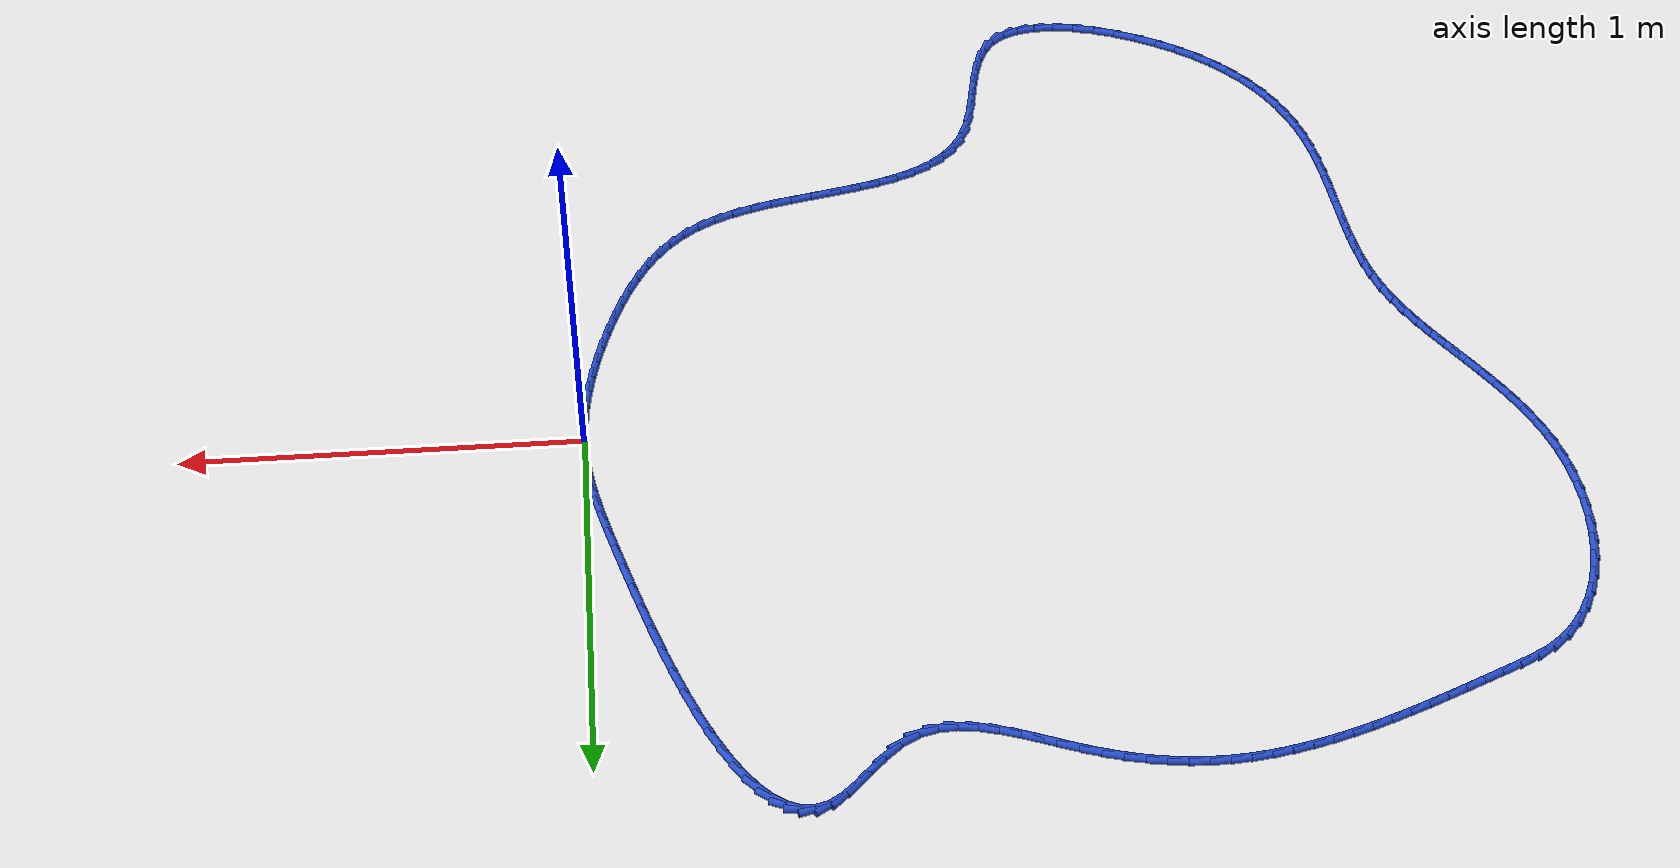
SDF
<sdf version="1.6">
 <world name="default">
  <light name="sun" type="directional">
   <pose>0 0 10 0 -0 0</pose>
   <diffuse>0.8 0.8 0.8 1</diffuse>
   <specular>0.2 0.2 0.2 1</specular>
   <attenuation>
    <range>1000</range>
    <constant>0.9</constant>
    <linear>0.01</linear>
    <quadratic>0.001</quadratic>
   </attenuation>
   <direction>-0.5 0.1 -0.9</direction>
  </light>
  <model name="ground_plane">
   <static>1</static>
   <link name="link">
    <collision name="collision">
     <geometry><plane><normal>0 0 1</normal><size>100 100</size></plane></geometry>
     <surface><friction><ode><mu>100</mu><mu2>50</mu2></ode></friction></surface>
    </collision>
    <visual name="visual">
     <cast_shadows>0</cast_shadows>
     <geometry><plane><normal>0 0 1</normal><size>100 100</size></plane></geometry>
     <material>
      <script><uri>file://media/materials/scripts/gazebo.material</uri><name>Gazebo/WhiteGlow</name></script>
     </material>
    </visual>
   </link>
  </model>
  <gravity>0 0 -9.8</gravity>
  <magnetic_field>6e-06 2.3e-05 -4.2e-05</magnetic_field>
  <atmosphere type="adiabatic"/>
  <physics name="default_physics" default="0" type="ode">
   <max_step_size>0.001</max_step_size>
   <real_time_factor>1</real_time_factor>
   <real_time_update_rate>1000</real_time_update_rate>
  </physics>
  <scene><ambient>0.4 0.4 0.4 1</ambient><background>0.7 0.7 0.7 1</background><shadows>1</shadows></scene>
  <spherical_coordinates>
   <surface_model>EARTH_WGS84</surface_model>
   <latitude_deg>0</latitude_deg>
   <longitude_deg>0</longitude_deg>
   <elevation>0</elevation>
   <heading_deg>0</heading_deg>
  </spherical_coordinates>
  <model name="line">
   <link name="link_0">
    <pose>6.938893903907228e-18 -3.469446951953614e-17 0.01 0 1.57 -1.5360227060647844</pose>
    <collision name="collision">
     <geometry><cylinder><radius>0.01</radius><length>0.08</length></cylinder></geometry>
    </collision>
    <visual name="visual">
     <material>
      <script><name>Gazebo/Blue</name><uri>file://media/materials/scripts/gazebo.material</uri></script>
     </material>
     <geometry><cylinder><radius>0.01</radius><length>0.08</length></cylinder></geometry>
    </visual>
   </link>
   <link name="link_1">
    <pose>-0.001596986714151066 0.04590672280092305 0.01 0 1.57 -1.475857038576187</pose>
    <collision name="collision">
     <geometry><cylinder><radius>0.01</radius><length>0.08</length></cylinder></geometry>
    </collision>
    <visual name="visual">
     <material>
      <script><name>Gazebo/Blue</name><uri>file://media/materials/scripts/gazebo.material</uri></script>
     </material>
     <geometry><cylinder><radius>0.01</radius><length>0.08</length></cylinder></geometry>
    </visual>
   </link>
   <link name="link_2">
    <pose>-0.005926904175951218 0.09137683878145414 0.01 0 1.57 -1.4215657157220285</pose>
    <collision name="collision">
     <geometry><cylinder><radius>0.01</radius><length>0.08</length></cylinder></geometry>
    </collision>
    <visual name="visual">
     <material>
      <script><name>Gazebo/Blue</name><uri>file://media/materials/scripts/gazebo.material</uri></script>
     </material>
     <geometry><cylinder><radius>0.01</radius><length>0.08</length></cylinder></geometry>
    </visual>
   </link>
   <link name="link_3">
    <pose>-0.012789451862567226 0.1370211565264232 0.01 0 1.57 -1.3752858160505892</pose>
    <collision name="collision">
     <geometry><cylinder><radius>0.01</radius><length>0.08</length></cylinder></geometry>
    </collision>
    <visual name="visual">
     <material>
      <script><name>Gazebo/Blue</name><uri>file://media/materials/scripts/gazebo.material</uri></script>
     </material>
     <geometry><cylinder><radius>0.01</radius><length>0.08</length></cylinder></geometry>
    </visual>
   </link>
   <link name="link_4">
    <pose>-0.02198432925116582 0.18345048462065977 0.01 0 1.57 -1.3382414032701597</pose>
    <collision name="collision">
     <geometry><cylinder><radius>0.01</radius><length>0.08</length></cylinder></geometry>
    </collision>
    <visual name="visual">
     <material>
      <script><name>Gazebo/Blue</name><uri>file://media/materials/scripts/gazebo.material</uri></script>
     </material>
     <geometry><cylinder><radius>0.01</radius><length>0.08</length></cylinder></geometry>
    </visual>
   </link>
   <link name="link_5">
    <pose>-0.033311235818913786 0.23127563164899403 0.01 0 1.57 -1.3107530400348604</pose>
    <collision name="collision">
     <geometry><cylinder><radius>0.01</radius><length>0.08</length></cylinder></geometry>
    </collision>
    <visual name="visual">
     <material>
      <script><name>Gazebo/Blue</name><uri>file://media/materials/scripts/gazebo.material</uri></script>
     </material>
     <geometry><cylinder><radius>0.01</radius><length>0.08</length></cylinder></geometry>
    </visual>
   </link>
   <link name="link_6">
    <pose>-0.046569871042977884 0.28110740619625574 0.01 0 1.57 -1.2924160326424814</pose>
    <collision name="collision">
     <geometry><cylinder><radius>0.01</radius><length>0.08</length></cylinder></geometry>
    </collision>
    <visual name="visual">
     <material>
      <script><name>Gazebo/Blue</name><uri>file://media/materials/scripts/gazebo.material</uri></script>
     </material>
     <geometry><cylinder><radius>0.01</radius><length>0.08</length></cylinder></geometry>
    </visual>
   </link>
   <link name="link_7">
    <pose>-0.06155993440052483 0.33355661684727456 0.01 0 1.57 -1.2823393863077601</pose>
    <collision name="collision">
     <geometry><cylinder><radius>0.01</radius><length>0.08</length></cylinder></geometry>
    </collision>
    <visual name="visual">
     <material>
      <script><name>Gazebo/Blue</name><uri>file://media/materials/scripts/gazebo.material</uri></script>
     </material>
     <geometry><cylinder><radius>0.01</radius><length>0.08</length></cylinder></geometry>
    </visual>
   </link>
   <link name="link_8">
    <pose>-0.078081163734985 0.3892336880036387 0.01 0 1.57 -1.2771850774956366</pose>
    <collision name="collision">
     <geometry><cylinder><radius>0.01</radius><length>0.08</length></cylinder></geometry>
    </collision>
    <visual name="visual">
     <material>
      <script><name>Gazebo/Blue</name><uri>file://media/materials/scripts/gazebo.material</uri></script>
     </material>
     <geometry><cylinder><radius>0.01</radius><length>0.08</length></cylinder></geometry>
    </visual>
   </link>
   <link name="link_9">
    <pose>-0.09596863491986994 0.4483951842516145 0.01 0 1.57 -1.2701571357892643</pose>
    <collision name="collision">
     <geometry><cylinder><radius>0.01</radius><length>0.08</length></cylinder></geometry>
    </collision>
    <visual name="visual">
     <material>
      <script><name>Gazebo/Blue</name><uri>file://media/materials/scripts/gazebo.material</uri></script>
     </material>
     <geometry><cylinder><radius>0.01</radius><length>0.08</length></cylinder></geometry>
    </visual>
   </link>
   <link name="link_10">
    <pose>-0.11515811464164638 0.5102893957378598 0.01 0 1.57 -1.2602094298435773</pose>
    <collision name="collision">
     <geometry><cylinder><radius>0.01</radius><length>0.08</length></cylinder></geometry>
    </collision>
    <visual name="visual">
     <material>
      <script><name>Gazebo/Blue</name><uri>file://media/materials/scripts/gazebo.material</uri></script>
     </material>
     <geometry><cylinder><radius>0.01</radius><length>0.08</length></cylinder></geometry>
    </visual>
   </link>
   <link name="link_11">
    <pose>-0.13560318512456432 0.5739862154857245 0.01 0 1.57 -1.2472190408617878</pose>
    <collision name="collision">
     <geometry><cylinder><radius>0.01</radius><length>0.08</length></cylinder></geometry>
    </collision>
    <visual name="visual">
     <material>
      <script><name>Gazebo/Blue</name><uri>file://media/materials/scripts/gazebo.material</uri></script>
     </material>
     <geometry><cylinder><radius>0.01</radius><length>0.08</length></cylinder></geometry>
    </visual>
   </link>
   <link name="link_12">
    <pose>-0.1572574285928738 0.6385555365185587 0.01 0 1.57 -1.2308400575151817</pose>
    <collision name="collision">
     <geometry><cylinder><radius>0.01</radius><length>0.08</length></cylinder></geometry>
    </collision>
    <visual name="visual">
     <material>
      <script><name>Gazebo/Blue</name><uri>file://media/materials/scripts/gazebo.material</uri></script>
     </material>
     <geometry><cylinder><radius>0.01</radius><length>0.08</length></cylinder></geometry>
    </visual>
   </link>
   <link name="link_13">
    <pose>-0.1800744272708248 0.7030672518597121 0.01 0 1.57 -1.210483083315057</pose>
    <collision name="collision">
     <geometry><cylinder><radius>0.01</radius><length>0.08</length></cylinder></geometry>
    </collision>
    <visual name="visual">
     <material>
      <script><name>Gazebo/Blue</name><uri>file://media/materials/scripts/gazebo.material</uri></script>
     </material>
     <geometry><cylinder><radius>0.01</radius><length>0.08</length></cylinder></geometry>
    </visual>
   </link>
   <link name="link_14">
    <pose>-0.20400776338266735 0.7665912545325347 0.01 0 1.57 -1.1852516564873345</pose>
    <collision name="collision">
     <geometry><cylinder><radius>0.01</radius><length>0.08</length></cylinder></geometry>
    </collision>
    <visual name="visual">
     <material>
      <script><name>Gazebo/Blue</name><uri>file://media/materials/scripts/gazebo.material</uri></script>
     </material>
     <geometry><cylinder><radius>0.01</radius><length>0.08</length></cylinder></geometry>
    </visual>
   </link>
   <link name="link_15">
    <pose>-0.2290110191526514 0.8281974375603767 0.01 0 1.57 -1.153823643787537</pose>
    <collision name="collision">
     <geometry><cylinder><radius>0.01</radius><length>0.08</length></cylinder></geometry>
    </collision>
    <visual name="visual">
     <material>
      <script><name>Gazebo/Blue</name><uri>file://media/materials/scripts/gazebo.material</uri></script>
     </material>
     <geometry><cylinder><radius>0.01</radius><length>0.08</length></cylinder></geometry>
    </visual>
   </link>
   <link name="link_16">
    <pose>-0.2550377768050271 0.886955693966588 0.01 0 1.57 -1.1142492763704</pose>
    <collision name="collision">
     <geometry><cylinder><radius>0.01</radius><length>0.08</length></cylinder></geometry>
    </collision>
    <visual name="visual">
     <material>
      <script><name>Gazebo/Blue</name><uri>file://media/materials/scripts/gazebo.material</uri></script>
     </material>
     <geometry><cylinder><radius>0.01</radius><length>0.08</length></cylinder></geometry>
    </visual>
   </link>
   <link name="link_17">
    <pose>-0.2820416185640443 0.9419359167745185 0.01 0 1.57 -1.0636131072509345</pose>
    <collision name="collision">
     <geometry><cylinder><radius>0.01</radius><length>0.08</length></cylinder></geometry>
    </collision>
    <visual name="visual">
     <material>
      <script><name>Gazebo/Blue</name><uri>file://media/materials/scripts/gazebo.material</uri></script>
     </material>
     <geometry><cylinder><radius>0.01</radius><length>0.08</length></cylinder></geometry>
    </visual>
   </link>
   <link name="link_18">
    <pose>-0.3099761266539531 0.9922079990075179 0.01 0 1.57 -0.9974706156892011</pose>
    <collision name="collision">
     <geometry><cylinder><radius>0.01</radius><length>0.08</length></cylinder></geometry>
    </collision>
    <visual name="visual">
     <material>
      <script><name>Gazebo/Blue</name><uri>file://media/materials/scripts/gazebo.material</uri></script>
     </material>
     <geometry><cylinder><radius>0.01</radius><length>0.08</length></cylinder></geometry>
    </visual>
   </link>
   <link name="link_19">
    <pose>-0.3387948832990036 1.0368418336889365 0.01 0 1.57 -0.9089335694575578</pose>
    <collision name="collision">
     <geometry><cylinder><radius>0.01</radius><length>0.08</length></cylinder></geometry>
    </collision>
    <visual name="visual">
     <material>
      <script><name>Gazebo/Blue</name><uri>file://media/materials/scripts/gazebo.material</uri></script>
     </material>
     <geometry><cylinder><radius>0.01</radius><length>0.08</length></cylinder></geometry>
    </visual>
   </link>
   <link name="link_20">
    <pose>-0.36845147072344564 1.0749073138421243 0.01 0 1.57 -0.7873487990125905</pose>
    <collision name="collision">
     <geometry><cylinder><radius>0.01</radius><length>0.08</length></cylinder></geometry>
    </collision>
    <visual name="visual">
     <material>
      <script><name>Gazebo/Blue</name><uri>file://media/materials/scripts/gazebo.material</uri></script>
     </material>
     <geometry><cylinder><radius>0.01</radius><length>0.08</length></cylinder></geometry>
    </visual>
   </link>
   <link name="link_21">
    <pose>-0.39889947115152935 1.105474332490431 0.01 0 1.57 -0.6172230626733947</pose>
    <collision name="collision">
     <geometry><cylinder><radius>0.01</radius><length>0.08</length></cylinder></geometry>
    </collision>
    <visual name="visual">
     <material>
      <script><name>Gazebo/Blue</name><uri>file://media/materials/scripts/gazebo.material</uri></script>
     </material>
     <geometry><cylinder><radius>0.01</radius><length>0.08</length></cylinder></geometry>
    </visual>
   </link>
   <link name="link_22">
    <pose>-0.4300924668075048 1.1276127826572069 0.01 0 1.57 -0.38113187126745024</pose>
    <collision name="collision">
     <geometry><cylinder><radius>0.01</radius><length>0.08</length></cylinder></geometry>
    </collision>
    <visual name="visual">
     <material>
      <script><name>Gazebo/Blue</name><uri>file://media/materials/scripts/gazebo.material</uri></script>
     </material>
     <geometry><cylinder><radius>0.01</radius><length>0.08</length></cylinder></geometry>
    </visual>
   </link>
   <link name="link_23">
    <pose>-0.46198403991562165 1.1403925573658011 0.01 0 1.57 -0.07639395772360699</pose>
    <collision name="collision">
     <geometry><cylinder><radius>0.01</radius><length>0.08</length></cylinder></geometry>
    </collision>
    <visual name="visual">
     <material>
      <script><name>Gazebo/Blue</name><uri>file://media/materials/scripts/gazebo.material</uri></script>
     </material>
     <geometry><cylinder><radius>0.01</radius><length>0.08</length></cylinder></geometry>
    </visual>
   </link>
   <link name="link_24">
    <pose>-0.4945277727001304 1.1428835496395648 0.01 0 1.57 0.2574464688038256</pose>
    <collision name="collision">
     <geometry><cylinder><radius>0.01</radius><length>0.08</length></cylinder></geometry>
    </collision>
    <visual name="visual">
     <material>
      <script><name>Gazebo/Blue</name><uri>file://media/materials/scripts/gazebo.material</uri></script>
     </material>
     <geometry><cylinder><radius>0.01</radius><length>0.08</length></cylinder></geometry>
    </visual>
   </link>
   <link name="link_25">
    <pose>-0.5276772473852805 1.134155652501847 0.01 0 1.57 0.5533277248231162</pose>
    <collision name="collision">
     <geometry><cylinder><radius>0.01</radius><length>0.08</length></cylinder></geometry>
    </collision>
    <visual name="visual">
     <material>
      <script><name>Gazebo/Blue</name><uri>file://media/materials/scripts/gazebo.material</uri></script>
     </material>
     <geometry><cylinder><radius>0.01</radius><length>0.08</length></cylinder></geometry>
    </visual>
   </link>
   <link name="link_26">
    <pose>-0.5613906061178655 1.113331140037228 0.01 0 1.57 0.7386219541332962</pose>
    <collision name="collision">
     <geometry><cylinder><radius>0.01</radius><length>0.08</length></cylinder></geometry>
    </collision>
    <visual name="visual">
     <material>
      <script><name>Gazebo/Blue</name><uri>file://media/materials/scripts/gazebo.material</uri></script>
     </material>
     <geometry><cylinder><radius>0.01</radius><length>0.08</length></cylinder></geometry>
    </visual>
   </link>
   <link name="link_27">
    <pose>-0.5958377445448142 1.0819647559505625 0.01 0 1.57 0.8032431050564621</pose>
    <collision name="collision">
     <geometry><cylinder><radius>0.01</radius><length>0.08</length></cylinder></geometry>
    </collision>
    <visual name="visual">
     <material>
      <script><name>Gazebo/Blue</name><uri>file://media/materials/scripts/gazebo.material</uri></script>
     </material>
     <geometry><cylinder><radius>0.01</radius><length>0.08</length></cylinder></geometry>
    </visual>
   </link>
   <link name="link_28">
    <pose>-0.6314854350822103 1.0450215475377622 0.01 0 1.57 0.784899751101055</pose>
    <collision name="collision">
     <geometry><cylinder><radius>0.01</radius><length>0.08</length></cylinder></geometry>
    </collision>
    <visual name="visual">
     <material>
      <script><name>Gazebo/Blue</name><uri>file://media/materials/scripts/gazebo.material</uri></script>
     </material>
     <geometry><cylinder><radius>0.01</radius><length>0.08</length></cylinder></geometry>
    </visual>
   </link>
   <link name="link_29">
    <pose>-0.6688226463902017 1.0077215363423155 0.01 0 1.57 0.6873306710897841</pose>
    <collision name="collision">
     <geometry><cylinder><radius>0.01</radius><length>0.08</length></cylinder></geometry>
    </collision>
    <visual name="visual">
     <material>
      <script><name>Gazebo/Blue</name><uri>file://media/materials/scripts/gazebo.material</uri></script>
     </material>
     <geometry><cylinder><radius>0.01</radius><length>0.08</length></cylinder></geometry>
    </visual>
   </link>
   <link name="link_30">
    <pose>-0.7083383471289351 0.9752847439077099 0.01 0 1.57 0.49031913403567523</pose>
    <collision name="collision">
     <geometry><cylinder><radius>0.01</radius><length>0.08</length></cylinder></geometry>
    </collision>
    <visual name="visual">
     <material>
      <script><name>Gazebo/Blue</name><uri>file://media/materials/scripts/gazebo.material</uri></script>
     </material>
     <geometry><cylinder><radius>0.01</radius><length>0.08</length></cylinder></geometry>
    </visual>
   </link>
   <link name="link_31">
    <pose>-0.7505010735535802 0.9527783587523594 0.01 0 1.57 0.23955699628761407</pose>
    <collision name="collision">
     <geometry><cylinder><radius>0.01</radius><length>0.08</length></cylinder></geometry>
    </collision>
    <visual name="visual">
     <material>
      <script><name>Gazebo/Blue</name><uri>file://media/materials/scripts/gazebo.material</uri></script>
     </material>
     <geometry><cylinder><radius>0.01</radius><length>0.08</length></cylinder></geometry>
    </visual>
   </link>
   <link name="link_32">
    <pose>-0.7953197265283377 0.9418315273577568 0.01 0 1.57 0.02453006478095447</pose>
    <collision name="collision">
     <geometry><cylinder><radius>0.01</radius><length>0.08</length></cylinder></geometry>
    </collision>
    <visual name="visual">
     <material>
      <script><name>Gazebo/Blue</name><uri>file://media/materials/scripts/gazebo.material</uri></script>
     </material>
     <geometry><cylinder><radius>0.01</radius><length>0.08</length></cylinder></geometry>
    </visual>
   </link>
   <link name="link_33">
    <pose>-0.8423492273311957 0.940677659210413 0.01 0 1.57 -0.1370744865808009</pose>
    <collision name="collision">
     <geometry><cylinder><radius>0.01</radius><length>0.08</length></cylinder></geometry>
    </collision>
    <visual name="visual">
     <material>
      <script><name>Gazebo/Blue</name><uri>file://media/materials/scripts/gazebo.material</uri></script>
     </material>
     <geometry><cylinder><radius>0.01</radius><length>0.08</length></cylinder></geometry>
    </visual>
   </link>
   <link name="link_34">
    <pose>-0.8911251960504718 0.9474057921867525 0.01 0 1.57 -0.24844751846264382</pose>
    <collision name="collision">
     <geometry><cylinder><radius>0.01</radius><length>0.08</length></cylinder></geometry>
    </collision>
    <visual name="visual">
     <material>
      <script><name>Gazebo/Blue</name><uri>file://media/materials/scripts/gazebo.material</uri></script>
     </material>
     <geometry><cylinder><radius>0.01</radius><length>0.08</length></cylinder></geometry>
    </visual>
   </link>
   <link name="link_35">
    <pose>-0.9411832527744834 0.9601049641631992 0.01 0 1.57 -0.3182200745731671</pose>
    <collision name="collision">
     <geometry><cylinder><radius>0.01</radius><length>0.08</length></cylinder></geometry>
    </collision>
    <visual name="visual">
     <material>
      <script><name>Gazebo/Blue</name><uri>file://media/materials/scripts/gazebo.material</uri></script>
     </material>
     <geometry><cylinder><radius>0.01</radius><length>0.08</length></cylinder></geometry>
    </visual>
   </link>
   <link name="link_36">
    <pose>-0.9920590175915496 0.9768642130161781 0.01 0 1.57 -0.3535829995147514</pose>
    <collision name="collision">
     <geometry><cylinder><radius>0.01</radius><length>0.08</length></cylinder></geometry>
    </collision>
    <visual name="visual">
     <material>
      <script><name>Gazebo/Blue</name><uri>file://media/materials/scripts/gazebo.material</uri></script>
     </material>
     <geometry><cylinder><radius>0.01</radius><length>0.08</length></cylinder></geometry>
    </visual>
   </link>
   <link name="link_37">
    <pose>-1.0432881105899872 0.995772576622113 0.01 0 1.57 -0.35838044684975473</pose>
    <collision name="collision">
     <geometry><cylinder><radius>0.01</radius><length>0.08</length></cylinder></geometry>
    </collision>
    <visual name="visual">
     <material>
      <script><name>Gazebo/Blue</name><uri>file://media/materials/scripts/gazebo.material</uri></script>
     </material>
     <geometry><cylinder><radius>0.01</radius><length>0.08</length></cylinder></geometry>
    </visual>
   </link>
   <link name="link_38">
    <pose>-1.0944061518581147 1.0149190928574288 0.01 0 1.57 -0.3331332674719621</pose>
    <collision name="collision">
     <geometry><cylinder><radius>0.01</radius><length>0.08</length></cylinder></geometry>
    </collision>
    <visual name="visual">
     <material>
      <script><name>Gazebo/Blue</name><uri>file://media/materials/scripts/gazebo.material</uri></script>
     </material>
     <geometry><cylinder><radius>0.01</radius><length>0.08</length></cylinder></geometry>
    </visual>
   </link>
   <link name="link_39">
    <pose>-1.1449543375437359 1.0324102569315232 0.01 0 1.57 -0.28739152608124247</pose>
    <collision name="collision">
     <geometry><cylinder><radius>0.01</radius><length>0.08</length></cylinder></geometry>
    </collision>
    <visual name="visual">
     <material>
      <script><name>Gazebo/Blue</name><uri>file://media/materials/scripts/gazebo.material</uri></script>
     </material>
     <geometry><cylinder><radius>0.01</radius><length>0.08</length></cylinder></geometry>
    </visual>
   </link>
   <link name="link_40">
    <pose>-1.1947187816008533 1.0471193441973832 0.01 0 1.57 -0.23681594599336975</pose>
    <collision name="collision">
     <geometry><cylinder><radius>0.01</radius><length>0.08</length></cylinder></geometry>
    </collision>
    <visual name="visual">
     <material>
      <script><name>Gazebo/Blue</name><uri>file://media/materials/scripts/gazebo.material</uri></script>
     </material>
     <geometry><cylinder><radius>0.01</radius><length>0.08</length></cylinder></geometry>
    </visual>
   </link>
   <link name="link_41">
    <pose>-1.2438210704948804 1.0589699156710368 0.01 0 1.57 -0.18299416979295743</pose>
    <collision name="collision">
     <geometry><cylinder><radius>0.01</radius><length>0.08</length></cylinder></geometry>
    </collision>
    <visual name="visual">
     <material>
      <script><name>Gazebo/Blue</name><uri>file://media/materials/scripts/gazebo.material</uri></script>
     </material>
     <geometry><cylinder><radius>0.01</radius><length>0.08</length></cylinder></geometry>
    </visual>
   </link>
   <link name="link_42">
    <pose>-1.2924070415312756 1.0679614560545014 0.01 0 1.57 -0.12649981398423962</pose>
    <collision name="collision">
     <geometry><cylinder><radius>0.01</radius><length>0.08</length></cylinder></geometry>
    </collision>
    <visual name="visual">
     <material>
      <script><name>Gazebo/Blue</name><uri>file://media/materials/scripts/gazebo.material</uri></script>
     </material>
     <geometry><cylinder><radius>0.01</radius><length>0.08</length></cylinder></geometry>
    </visual>
   </link>
   <link name="link_43">
    <pose>-1.3406225320154967 1.0740934500497934 0.01 0 1.57 -0.06807291339887869</pose>
    <collision name="collision">
     <geometry><cylinder><radius>0.01</radius><length>0.08</length></cylinder></geometry>
    </collision>
    <visual name="visual">
     <material>
      <script><name>Gazebo/Blue</name><uri>file://media/materials/scripts/gazebo.material</uri></script>
     </material>
     <geometry><cylinder><radius>0.01</radius><length>0.08</length></cylinder></geometry>
    </visual>
   </link>
   <link name="link_44">
    <pose>-1.3886133792530029 1.0773653823589304 0.01 0 1.57 -0.008606541192220565</pose>
    <collision name="collision">
     <geometry><cylinder><radius>0.01</radius><length>0.08</length></cylinder></geometry>
    </collision>
    <visual name="visual">
     <material>
      <script><name>Gazebo/Blue</name><uri>file://media/materials/scripts/gazebo.material</uri></script>
     </material>
     <geometry><cylinder><radius>0.01</radius><length>0.08</length></cylinder></geometry>
    </visual>
   </link>
   <link name="link_45">
    <pose>-1.4365246318945821 1.077777742709939 0.01 0 1.57 0.049498626090179035</pose>
    <collision name="collision">
     <geometry><cylinder><radius>0.01</radius><length>0.08</length></cylinder></geometry>
    </collision>
    <visual name="visual">
     <material>
      <script><name>Gazebo/Blue</name><uri>file://media/materials/scripts/gazebo.material</uri></script>
     </material>
     <geometry><cylinder><radius>0.01</radius><length>0.08</length></cylinder></geometry>
    </visual>
   </link>
   <link name="link_46">
    <pose>-1.484444187621647 1.0754038514537885 0.01 0 1.57 0.10326179931639413</pose>
    <collision name="collision">
     <geometry><cylinder><radius>0.01</radius><length>0.08</length></cylinder></geometry>
    </collision>
    <visual name="visual">
     <material>
      <script><name>Gazebo/Blue</name><uri>file://media/materials/scripts/gazebo.material</uri></script>
     </material>
     <geometry><cylinder><radius>0.01</radius><length>0.08</length></cylinder></geometry>
    </visual>
   </link>
   <link name="link_47">
    <pose>-1.5323651903711109 1.070437778848447 0.01 0 1.57 0.15229372753024786</pose>
    <collision name="collision">
     <geometry><cylinder><radius>0.01</radius><length>0.08</length></cylinder></geometry>
    </collision>
    <visual name="visual">
     <material>
      <script><name>Gazebo/Blue</name><uri>file://media/materials/scripts/gazebo.material</uri></script>
     </material>
     <geometry><cylinder><radius>0.01</radius><length>0.08</length></cylinder></geometry>
    </visual>
   </link>
   <link name="link_48">
    <pose>-1.5802718668736737 1.0630849588381084 0.01 0 1.57 0.19656833805115623</pose>
    <collision name="collision">
     <geometry><cylinder><radius>0.01</radius><length>0.08</length></cylinder></geometry>
    </collision>
    <visual name="visual">
     <material>
      <script><name>Gazebo/Blue</name><uri>file://media/materials/scripts/gazebo.material</uri></script>
     </material>
     <geometry><cylinder><radius>0.01</radius><length>0.08</length></cylinder></geometry>
    </visual>
   </link>
   <link name="link_49">
    <pose>-1.6281484438600338 1.0535508253669692 0.01 0 1.57 0.2361506753977911</pose>
    <collision name="collision">
     <geometry><cylinder><radius>0.01</radius><length>0.08</length></cylinder></geometry>
    </collision>
    <visual name="visual">
     <material>
      <script><name>Gazebo/Blue</name><uri>file://media/materials/scripts/gazebo.material</uri></script>
     </material>
     <geometry><cylinder><radius>0.01</radius><length>0.08</length></cylinder></geometry>
    </visual>
   </link>
   <link name="link_50">
    <pose>-1.6759791480608908 1.0420408123792244 0.01 0 1.57 0.27116597516490126</pose>
    <collision name="collision">
     <geometry><cylinder><radius>0.01</radius><length>0.08</length></cylinder></geometry>
    </collision>
    <visual name="visual">
     <material>
      <script><name>Gazebo/Blue</name><uri>file://media/materials/scripts/gazebo.material</uri></script>
     </material>
     <geometry><cylinder><radius>0.01</radius><length>0.08</length></cylinder></geometry>
    </visual>
   </link>
   <link name="link_51">
    <pose>-1.7237482062069434 1.0287603538190693 0.01 0 1.57 0.30177334579369913</pose>
    <collision name="collision">
     <geometry><cylinder><radius>0.01</radius><length>0.08</length></cylinder></geometry>
    </collision>
    <visual name="visual">
     <material>
      <script><name>Gazebo/Blue</name><uri>file://media/materials/scripts/gazebo.material</uri></script>
     </material>
     <geometry><cylinder><radius>0.01</radius><length>0.08</length></cylinder></geometry>
    </visual>
   </link>
   <link name="link_52">
    <pose>-1.7714398450288904 1.013914883630699 0.01 0 1.57 0.3281447749035978</pose>
    <collision name="collision">
     <geometry><cylinder><radius>0.01</radius><length>0.08</length></cylinder></geometry>
    </collision>
    <visual name="visual">
     <material>
      <script><name>Gazebo/Blue</name><uri>file://media/materials/scripts/gazebo.material</uri></script>
     </material>
     <geometry><cylinder><radius>0.01</radius><length>0.08</length></cylinder></geometry>
    </visual>
   </link>
   <link name="link_53">
    <pose>-1.8190382912574317 0.9977098357583087 0.01 0 1.57 0.3504491888019872</pose>
    <collision name="collision">
     <geometry><cylinder><radius>0.01</radius><length>0.08</length></cylinder></geometry>
    </collision>
    <visual name="visual">
     <material>
      <script><name>Gazebo/Blue</name><uri>file://media/materials/scripts/gazebo.material</uri></script>
     </material>
     <geometry><cylinder><radius>0.01</radius><length>0.08</length></cylinder></geometry>
    </visual>
   </link>
   <link name="link_54">
    <pose>-1.8665277716232649 0.9803506441460944 0.01 0 1.57 0.36884079617444926</pose>
    <collision name="collision">
     <geometry><cylinder><radius>0.01</radius><length>0.08</length></cylinder></geometry>
    </collision>
    <visual name="visual">
     <material>
      <script><name>Gazebo/Blue</name><uri>file://media/materials/scripts/gazebo.material</uri></script>
     </material>
     <geometry><cylinder><radius>0.01</radius><length>0.08</length></cylinder></geometry>
    </visual>
   </link>
   <link name="link_55">
    <pose>-1.9138925128570894 0.9620427427382504 0.01 0 1.57 0.3834507866975855</pose>
    <collision name="collision">
     <geometry><cylinder><radius>0.01</radius><length>0.08</length></cylinder></geometry>
    </collision>
    <visual name="visual">
     <material>
      <script><name>Gazebo/Blue</name><uri>file://media/materials/scripts/gazebo.material</uri></script>
     </material>
     <geometry><cylinder><radius>0.01</radius><length>0.08</length></cylinder></geometry>
    </visual>
   </link>
   <link name="link_56">
    <pose>-1.9611167416896054 0.9429915654789724 0.01 0 1.57 0.3943814908346376</pose>
    <collision name="collision">
     <geometry><cylinder><radius>0.01</radius><length>0.08</length></cylinder></geometry>
    </collision>
    <visual name="visual">
     <material>
      <script><name>Gazebo/Blue</name><uri>file://media/materials/scripts/gazebo.material</uri></script>
     </material>
     <geometry><cylinder><radius>0.01</radius><length>0.08</length></cylinder></geometry>
    </visual>
   </link>
   <link name="link_57">
    <pose>-2.0081846848515106 0.923402546312456 0.01 0 1.57 0.40170223621884027</pose>
    <collision name="collision">
     <geometry><cylinder><radius>0.01</radius><length>0.08</length></cylinder></geometry>
    </collision>
    <visual name="visual">
     <material>
      <script><name>Gazebo/Blue</name><uri>file://media/materials/scripts/gazebo.material</uri></script>
     </material>
     <geometry><cylinder><radius>0.01</radius><length>0.08</length></cylinder></geometry>
    </visual>
   </link>
   <link name="link_58">
    <pose>-2.0550805690735046 0.903481119182896 0.01 0 1.57 0.4054462970298465</pose>
    <collision name="collision">
     <geometry><cylinder><radius>0.01</radius><length>0.08</length></cylinder></geometry>
    </collision>
    <visual name="visual">
     <material>
      <script><name>Gazebo/Blue</name><uri>file://media/materials/scripts/gazebo.material</uri></script>
     </material>
     <geometry><cylinder><radius>0.01</radius><length>0.08</length></cylinder></geometry>
    </visual>
   </link>
   <link name="link_59">
    <pose>-2.1017886210862855 0.883432718034488 0.01 0 1.57 0.40563265341808996</pose>
    <collision name="collision">
     <geometry><cylinder><radius>0.01</radius><length>0.08</length></cylinder></geometry>
    </collision>
    <visual name="visual">
     <material>
      <script><name>Gazebo/Blue</name><uri>file://media/materials/scripts/gazebo.material</uri></script>
     </material>
     <geometry><cylinder><radius>0.01</radius><length>0.08</length></cylinder></geometry>
    </visual>
   </link>
   <link name="link_60">
    <pose>-2.148292374266204 0.8634617439169077 0.01 0 1.57 0.41788803237292255</pose>
    <collision name="collision">
     <geometry><cylinder><radius>0.01</radius><length>0.08</length></cylinder></geometry>
    </collision>
    <visual name="visual">
     <material>
      <script><name>Gazebo/Blue</name><uri>file://media/materials/scripts/gazebo.material</uri></script>
     </material>
     <geometry><cylinder><radius>0.01</radius><length>0.08</length></cylinder></geometry>
    </visual>
   </link>
   <link name="link_61">
    <pose>-2.1941293711009187 0.8431082023291221 0.01 0 1.57 0.48643858706138365</pose>
    <collision name="collision">
     <geometry><cylinder><radius>0.01</radius><length>0.08</length></cylinder></geometry>
    </collision>
    <visual name="visual">
     <material>
      <script><name>Gazebo/Blue</name><uri>file://media/materials/scripts/gazebo.material</uri></script>
     </material>
     <geometry><cylinder><radius>0.01</radius><length>0.08</length></cylinder></geometry>
    </visual>
   </link>
   <link name="link_62">
    <pose>-2.2376252007400925 0.8201066439371746 0.01 0 1.57 0.6198283572296684</pose>
    <collision name="collision">
     <geometry><cylinder><radius>0.01</radius><length>0.08</length></cylinder></geometry>
    </collision>
    <visual name="visual">
     <material>
      <script><name>Gazebo/Blue</name><uri>file://media/materials/scripts/gazebo.material</uri></script>
     </material>
     <geometry><cylinder><radius>0.01</radius><length>0.08</length></cylinder></geometry>
    </visual>
   </link>
   <link name="link_63">
    <pose>-2.2769815223140015 0.7920200083857877 0.01 0 1.57 0.7752657073368754</pose>
    <collision name="collision">
     <geometry><cylinder><radius>0.01</radius><length>0.08</length></cylinder></geometry>
    </collision>
    <visual name="visual">
     <material>
      <script><name>Gazebo/Blue</name><uri>file://media/materials/scripts/gazebo.material</uri></script>
     </material>
     <geometry><cylinder><radius>0.01</radius><length>0.08</length></cylinder></geometry>
    </visual>
   </link>
   <link name="link_64">
    <pose>-2.3114867878918157 0.7582069984237031 0.01 0 1.57 0.9181077371622427</pose>
    <collision name="collision">
     <geometry><cylinder><radius>0.01</radius><length>0.08</length></cylinder></geometry>
    </collision>
    <visual name="visual">
     <material>
      <script><name>Gazebo/Blue</name><uri>file://media/materials/scripts/gazebo.material</uri></script>
     </material>
     <geometry><cylinder><radius>0.01</radius><length>0.08</length></cylinder></geometry>
    </visual>
   </link>
   <link name="link_65">
    <pose>-2.341213171636389 0.7193213005718867 0.01 0 1.57 1.0463045350356581</pose>
    <collision name="collision">
     <geometry><cylinder><radius>0.01</radius><length>0.08</length></cylinder></geometry>
    </collision>
    <visual name="visual">
     <material>
      <script><name>Gazebo/Blue</name><uri>file://media/materials/scripts/gazebo.material</uri></script>
     </material>
     <geometry><cylinder><radius>0.01</radius><length>0.08</length></cylinder></geometry>
    </visual>
   </link>
   <link name="link_66">
    <pose>-2.36625017567037 0.6760452332182856 0.01 0 1.57 1.1605034433810284</pose>
    <collision name="collision">
     <geometry><cylinder><radius>0.01</radius><length>0.08</length></cylinder></geometry>
    </collision>
    <visual name="visual">
     <material>
      <script><name>Gazebo/Blue</name><uri>file://media/materials/scripts/gazebo.material</uri></script>
     </material>
     <geometry><cylinder><radius>0.01</radius><length>0.08</length></cylinder></geometry>
    </visual>
   </link>
   <link name="link_67">
    <pose>-2.386687302116405 0.6290611147508475 0.01 0 1.57 1.2624798153386554</pose>
    <collision name="collision">
     <geometry><cylinder><radius>0.01</radius><length>0.08</length></cylinder></geometry>
    </collision>
    <visual name="visual">
     <material>
      <script><name>Gazebo/Blue</name><uri>file://media/materials/scripts/gazebo.material</uri></script>
     </material>
     <geometry><cylinder><radius>0.01</radius><length>0.08</length></cylinder></geometry>
    </visual>
   </link>
   <link name="link_68">
    <pose>-2.402614053097141 0.579051263557519 0.01 0 1.57 1.3544617615261798</pose>
    <collision name="collision">
     <geometry><cylinder><radius>0.01</radius><length>0.08</length></cylinder></geometry>
    </collision>
    <visual name="visual">
     <material>
      <script><name>Gazebo/Blue</name><uri>file://media/materials/scripts/gazebo.material</uri></script>
     </material>
     <geometry><cylinder><radius>0.01</radius><length>0.08</length></cylinder></geometry>
    </visual>
   </link>
   <link name="link_69">
    <pose>-2.414119930735223 0.5266979980262476 0.01 0 1.57 1.4387433930792604</pose>
    <collision name="collision">
     <geometry><cylinder><radius>0.01</radius><length>0.08</length></cylinder></geometry>
    </collision>
    <visual name="visual">
     <material>
      <script><name>Gazebo/Blue</name><uri>file://media/materials/scripts/gazebo.material</uri></script>
     </material>
     <geometry><cylinder><radius>0.01</radius><length>0.08</length></cylinder></geometry>
    </visual>
   </link>
   <link name="link_70">
    <pose>-2.421294437153301 0.47268363654498075 0.01 0 1.57 1.5175194606865092</pose>
    <collision name="collision">
     <geometry><cylinder><radius>0.01</radius><length>0.08</length></cylinder></geometry>
    </collision>
    <visual name="visual">
     <material>
      <script><name>Gazebo/Blue</name><uri>file://media/materials/scripts/gazebo.material</uri></script>
     </material>
     <geometry><cylinder><radius>0.01</radius><length>0.08</length></cylinder></geometry>
    </visual>
   </link>
   <link name="link_71">
    <pose>-2.4242270744740204 0.4176904975016647 0.01 0 1.57 -1.5487391608929284</pose>
    <collision name="collision">
     <geometry><cylinder><radius>0.01</radius><length>0.08</length></cylinder></geometry>
    </collision>
    <visual name="visual">
     <material>
      <script><name>Gazebo/Blue</name><uri>file://media/materials/scripts/gazebo.material</uri></script>
     </material>
     <geometry><cylinder><radius>0.01</radius><length>0.08</length></cylinder></geometry>
    </visual>
   </link>
   <link name="link_72">
    <pose>-2.423007344820028 0.36240089928424774 0.01 0 1.57 -1.4748760223154675</pose>
    <collision name="collision">
     <geometry><cylinder><radius>0.01</radius><length>0.08</length></cylinder></geometry>
    </collision>
    <visual name="visual">
     <material>
      <script><name>Gazebo/Blue</name><uri>file://media/materials/scripts/gazebo.material</uri></script>
     </material>
     <geometry><cylinder><radius>0.01</radius><length>0.08</length></cylinder></geometry>
    </visual>
   </link>
   <link name="link_73">
    <pose>-2.417724750313972 0.30749716028067614 0.01 0 1.57 -1.4005308148073337</pose>
    <collision name="collision">
     <geometry><cylinder><radius>0.01</radius><length>0.08</length></cylinder></geometry>
    </collision>
    <visual name="visual">
     <material>
      <script><name>Gazebo/Blue</name><uri>file://media/materials/scripts/gazebo.material</uri></script>
     </material>
     <geometry><cylinder><radius>0.01</radius><length>0.08</length></cylinder></geometry>
    </visual>
   </link>
   <link name="link_74">
    <pose>-2.408468793078497 0.2536615988788979 0.01 0 1.57 -1.3236765897014144</pose>
    <collision name="collision">
     <geometry><cylinder><radius>0.01</radius><length>0.08</length></cylinder></geometry>
    </collision>
    <visual name="visual">
     <material>
      <script><name>Gazebo/Blue</name><uri>file://media/materials/scripts/gazebo.material</uri></script>
     </material>
     <geometry><cylinder><radius>0.01</radius><length>0.08</length></cylinder></geometry>
    </visual>
   </link>
   <link name="link_75">
    <pose>-2.3953289752362528 0.20157653346685991 0.01 0 1.57 -1.2436698901764756</pose>
    <collision name="collision">
     <geometry><cylinder><radius>0.01</radius><length>0.08</length></cylinder></geometry>
    </collision>
    <visual name="visual">
     <material>
      <script><name>Gazebo/Blue</name><uri>file://media/materials/scripts/gazebo.material</uri></script>
     </material>
     <geometry><cylinder><radius>0.01</radius><length>0.08</length></cylinder></geometry>
    </visual>
   </link>
   <link name="link_76">
    <pose>-2.378444381178982 0.15181604900090914 0.01 0 1.57 -1.1688323779469503</pose>
    <collision name="collision">
     <geometry><cylinder><radius>0.01</radius><length>0.08</length></cylinder></geometry>
    </collision>
    <visual name="visual">
     <material>
      <script><name>Gazebo/Blue</name><uri>file://media/materials/scripts/gazebo.material</uri></script>
     </material>
     <geometry><cylinder><radius>0.01</radius><length>0.08</length></cylinder></geometry>
    </visual>
   </link>
   <link name="link_77">
    <pose>-2.3582491461271853 0.10431016221963244 0.01 0 1.57 -1.1039270451371417</pose>
    <collision name="collision">
     <geometry><cylinder><radius>0.01</radius><length>0.08</length></cylinder></geometry>
    </collision>
    <visual name="visual">
     <material>
      <script><name>Gazebo/Blue</name><uri>file://media/materials/scripts/gazebo.material</uri></script>
     </material>
     <geometry><cylinder><radius>0.01</radius><length>0.08</length></cylinder></geometry>
    </visual>
   </link>
   <link name="link_78">
    <pose>-2.335286104644336 0.058751609416068155 0.01 0 1.57 -1.0500835560835633</pose>
    <collision name="collision">
     <geometry><cylinder><radius>0.01</radius><length>0.08</length></cylinder></geometry>
    </collision>
    <visual name="visual">
     <material>
      <script><name>Gazebo/Blue</name><uri>file://media/materials/scripts/gazebo.material</uri></script>
     </material>
     <geometry><cylinder><radius>0.01</radius><length>0.08</length></cylinder></geometry>
    </visual>
   </link>
   <link name="link_79">
    <pose>-2.3100982616329895 0.014832755049058795 0.01 0 1.57 -1.0079381348653917</pose>
    <collision name="collision">
     <geometry><cylinder><radius>0.01</radius><length>0.08</length></cylinder></geometry>
    </collision>
    <visual name="visual">
     <material>
      <script><name>Gazebo/Blue</name><uri>file://media/materials/scripts/gazebo.material</uri></script>
     </material>
     <geometry><cylinder><radius>0.01</radius><length>0.08</length></cylinder></geometry>
    </visual>
   </link>
   <link name="link_80">
    <pose>-2.2832286219957028 -0.027754036422554085 0.01 0 1.57 -0.9778101112877265</pose>
    <collision name="collision">
     <geometry><cylinder><radius>0.01</radius><length>0.08</length></cylinder></geometry>
    </collision>
    <visual name="visual">
     <material>
      <script><name>Gazebo/Blue</name><uri>file://media/materials/scripts/gazebo.material</uri></script>
     </material>
     <geometry><cylinder><radius>0.01</radius><length>0.08</length></cylinder></geometry>
    </visual>
   </link>
   <link name="link_81">
    <pose>-2.2552201906350313 -0.06931640053992877 0.01 0 1.57 -0.9598679988964594</pose>
    <collision name="collision">
     <geometry><cylinder><radius>0.01</radius><length>0.08</length></cylinder></geometry>
    </collision>
    <visual name="visual">
     <material>
      <script><name>Gazebo/Blue</name><uri>file://media/materials/scripts/gazebo.material</uri></script>
     </material>
     <geometry><cylinder><radius>0.01</radius><length>0.08</length></cylinder></geometry>
    </visual>
   </link>
   <link name="link_82">
    <pose>-2.2266159724535295 -0.11016197284422416 0.01 0 1.57 -0.9542600099068724</pose>
    <collision name="collision">
     <geometry><cylinder><radius>0.01</radius><length>0.08</length></cylinder></geometry>
    </collision>
    <visual name="visual">
     <material>
      <script><name>Gazebo/Blue</name><uri>file://media/materials/scripts/gazebo.material</uri></script>
     </material>
     <geometry><cylinder><radius>0.01</radius><length>0.08</length></cylinder></geometry>
    </visual>
   </link>
   <link name="link_83">
    <pose>-2.1979589723537565 -0.1505983888765969 0.01 0 1.57 -0.9611968856418122</pose>
    <collision name="collision">
     <geometry><cylinder><radius>0.01</radius><length>0.08</length></cylinder></geometry>
    </collision>
    <visual name="visual">
     <material>
      <script><name>Gazebo/Blue</name><uri>file://media/materials/scripts/gazebo.material</uri></script>
     </material>
     <geometry><cylinder><radius>0.01</radius><length>0.08</length></cylinder></geometry>
    </visual>
   </link>
   <link name="link_84">
    <pose>-2.169792195238266 -0.190933284178206 0.01 0 1.57 -0.9809822110516195</pose>
    <collision name="collision">
     <geometry><cylinder><radius>0.01</radius><length>0.08</length></cylinder></geometry>
    </collision>
    <visual name="visual">
     <material>
      <script><name>Gazebo/Blue</name><uri>file://media/materials/scripts/gazebo.material</uri></script>
     </material>
     <geometry><cylinder><radius>0.01</radius><length>0.08</length></cylinder></geometry>
    </visual>
   </link>
   <link name="link_85">
    <pose>-2.1426586460096146 -0.2314742942902095 0.01 0 1.57 -1.0139840036874994</pose>
    <collision name="collision">
     <geometry><cylinder><radius>0.01</radius><length>0.08</length></cylinder></geometry>
    </collision>
    <visual name="visual">
     <material>
      <script><name>Gazebo/Blue</name><uri>file://media/materials/scripts/gazebo.material</uri></script>
     </material>
     <geometry><cylinder><radius>0.01</radius><length>0.08</length></cylinder></geometry>
    </visual>
   </link>
   <link name="link_86">
    <pose>-2.1171013295703585 -0.2725290547537657 0.01 0 1.57 -1.0605364208073869</pose>
    <collision name="collision">
     <geometry><cylinder><radius>0.01</radius><length>0.08</length></cylinder></geometry>
    </collision>
    <visual name="visual">
     <material>
      <script><name>Gazebo/Blue</name><uri>file://media/materials/scripts/gazebo.material</uri></script>
     </material>
     <geometry><cylinder><radius>0.01</radius><length>0.08</length></cylinder></geometry>
    </visual>
   </link>
   <link name="link_87">
    <pose>-2.093663250823052 -0.31440520111003345 0.01 0 1.57 -1.1207591479602437</pose>
    <collision name="collision">
     <geometry><cylinder><radius>0.01</radius><length>0.08</length></cylinder></geometry>
    </collision>
    <visual name="visual">
     <material>
      <script><name>Gazebo/Blue</name><uri>file://media/materials/scripts/gazebo.material</uri></script>
     </material>
     <geometry><cylinder><radius>0.01</radius><length>0.08</length></cylinder></geometry>
    </visual>
   </link>
   <link name="link_88">
    <pose>-2.0728874146702534 -0.35741036890016953 0.01 0 1.57 -1.1942729933772807</pose>
    <collision name="collision">
     <geometry><cylinder><radius>0.01</radius><length>0.08</length></cylinder></geometry>
    </collision>
    <visual name="visual">
     <material>
      <script><name>Gazebo/Blue</name><uri>file://media/materials/scripts/gazebo.material</uri></script>
     </material>
     <geometry><cylinder><radius>0.01</radius><length>0.08</length></cylinder></geometry>
    </visual>
   </link>
   <link name="link_89">
    <pose>-2.055315884047986 -0.40185171590787255 0.01 0 1.57 -1.2730362494754968</pose>
    <collision name="collision">
     <geometry><cylinder><radius>0.01</radius><length>0.08</length></cylinder></geometry>
    </collision>
    <visual name="visual">
     <material>
      <script><name>Gazebo/Blue</name><uri>file://media/materials/scripts/gazebo.material</uri></script>
     </material>
     <geometry><cylinder><radius>0.01</radius><length>0.08</length></cylinder></geometry>
    </visual>
   </link>
   <link name="link_90">
    <pose>-2.041189450497938 -0.4478835976129128 0.01 0 1.57 -1.339370322055567</pose>
    <collision name="collision">
     <geometry><cylinder><radius>0.01</radius><length>0.08</length></cylinder></geometry>
    </collision>
    <visual name="visual">
     <material>
      <script><name>Gazebo/Blue</name><uri>file://media/materials/scripts/gazebo.material</uri></script>
     </material>
     <geometry><cylinder><radius>0.01</radius><length>0.08</length></cylinder></geometry>
    </visual>
   </link>
   <link name="link_91">
    <pose>-2.030018271830909 -0.49528979824433395 0.01 0 1.57 -1.3910523452875432</pose>
    <collision name="collision">
     <geometry><cylinder><radius>0.01</radius><length>0.08</length></cylinder></geometry>
    </collision>
    <visual name="visual">
     <material>
      <script><name>Gazebo/Blue</name><uri>file://media/materials/scripts/gazebo.material</uri></script>
     </material>
     <geometry><cylinder><radius>0.01</radius><length>0.08</length></cylinder></geometry>
    </visual>
   </link>
   <link name="link_92">
    <pose>-2.021203901689202 -0.5437990189151798 0.01 0 1.57 -1.4287542443343206</pose>
    <collision name="collision">
     <geometry><cylinder><radius>0.01</radius><length>0.08</length></cylinder></geometry>
    </collision>
    <visual name="visual">
     <material>
      <script><name>Gazebo/Blue</name><uri>file://media/materials/scripts/gazebo.material</uri></script>
     </material>
     <geometry><cylinder><radius>0.01</radius><length>0.08</length></cylinder></geometry>
    </visual>
   </link>
   <link name="link_93">
    <pose>-2.0141478937151214 -0.5931399607384914 0.01 0 1.57 -1.4531866743383088</pose>
    <collision name="collision">
     <geometry><cylinder><radius>0.01</radius><length>0.08</length></cylinder></geometry>
    </collision>
    <visual name="visual">
     <material>
      <script><name>Gazebo/Blue</name><uri>file://media/materials/scripts/gazebo.material</uri></script>
     </material>
     <geometry><cylinder><radius>0.01</radius><length>0.08</length></cylinder></geometry>
    </visual>
   </link>
   <link name="link_94">
    <pose>-2.008251801550974 -0.6430413248273128 0.01 0 1.57 -1.4649063548800945</pose>
    <collision name="collision">
     <geometry><cylinder><radius>0.01</radius><length>0.08</length></cylinder></geometry>
    </collision>
    <visual name="visual">
     <material>
      <script><name>Gazebo/Blue</name><uri>file://media/materials/scripts/gazebo.material</uri></script>
     </material>
     <geometry><cylinder><radius>0.01</radius><length>0.08</length></cylinder></geometry>
    </visual>
   </link>
   <link name="link_95">
    <pose>-2.002917178839063 -0.6932318122946868 0.01 0 1.57 -1.4642154746181058</pose>
    <collision name="collision">
     <geometry><cylinder><radius>0.01</radius><length>0.08</length></cylinder></geometry>
    </collision>
    <visual name="visual">
     <material>
      <script><name>Gazebo/Blue</name><uri>file://media/materials/scripts/gazebo.material</uri></script>
     </material>
     <geometry><cylinder><radius>0.01</radius><length>0.08</length></cylinder></geometry>
    </visual>
   </link>
   <link name="link_96">
    <pose>-1.997545579221694 -0.7434401242536572 0.01 0 1.57 -1.4511218713122471</pose>
    <collision name="collision">
     <geometry><cylinder><radius>0.01</radius><length>0.08</length></cylinder></geometry>
    </collision>
    <visual name="visual">
     <material>
      <script><name>Gazebo/Blue</name><uri>file://media/materials/scripts/gazebo.material</uri></script>
     </material>
     <geometry><cylinder><radius>0.01</radius><length>0.08</length></cylinder></geometry>
    </visual>
   </link>
   <link name="link_97">
    <pose>-1.9915385563411712 -0.7933949618172651 0.01 0 1.57 -1.4253432264457444</pose>
    <collision name="collision">
     <geometry><cylinder><radius>0.01</radius><length>0.08</length></cylinder></geometry>
    </collision>
    <visual name="visual">
     <material>
      <script><name>Gazebo/Blue</name><uri>file://media/materials/scripts/gazebo.material</uri></script>
     </material>
     <geometry><cylinder><radius>0.01</radius><length>0.08</length></cylinder></geometry>
    </visual>
   </link>
   <link name="link_98">
    <pose>-1.9842976638397993 -0.8428250260985547 0.01 0 1.57 -1.3863555950399609</pose>
    <collision name="collision">
     <geometry><cylinder><radius>0.01</radius><length>0.08</length></cylinder></geometry>
    </collision>
    <visual name="visual">
     <material>
      <script><name>Gazebo/Blue</name><uri>file://media/materials/scripts/gazebo.material</uri></script>
     </material>
     <geometry><cylinder><radius>0.01</radius><length>0.08</length></cylinder></geometry>
    </visual>
   </link>
   <link name="link_99">
    <pose>-1.975224455359884 -0.8914590182105686 0.01 0 1.57 -1.3335031657812735</pose>
    <collision name="collision">
     <geometry><cylinder><radius>0.01</radius><length>0.08</length></cylinder></geometry>
    </collision>
    <visual name="visual">
     <material>
      <script><name>Gazebo/Blue</name><uri>file://media/materials/scripts/gazebo.material</uri></script>
     </material>
     <geometry><cylinder><radius>0.01</radius><length>0.08</length></cylinder></geometry>
    </visual>
   </link>
   <link name="link_100">
    <pose>-1.9637204845437288 -0.9390256392663499 0.01 0 1.57 -1.2669470118805266</pose>
    <collision name="collision">
     <geometry><cylinder><radius>0.01</radius><length>0.08</length></cylinder></geometry>
    </collision>
    <visual name="visual">
     <material>
      <script><name>Gazebo/Blue</name><uri>file://media/materials/scripts/gazebo.material</uri></script>
     </material>
     <geometry><cylinder><radius>0.01</radius><length>0.08</length></cylinder></geometry>
    </visual>
   </link>
   <link name="link_101">
    <pose>-1.949220175683718 -0.98526992235297 0.01 0 1.57 -1.1927419523669363</pose>
    <collision name="collision">
     <geometry><cylinder><radius>0.01</radius><length>0.08</length></cylinder></geometry>
    </collision>
    <visual name="visual">
     <material>
      <script><name>Gazebo/Blue</name><uri>file://media/materials/scripts/gazebo.material</uri></script>
     </material>
     <geometry><cylinder><radius>0.01</radius><length>0.08</length></cylinder></geometry>
    </visual>
   </link>
   <link name="link_102">
    <pose>-1.9314271806730055 -1.0300706678597187 0.01 0 1.57 -1.1145753081560361</pose>
    <collision name="collision">
     <geometry><cylinder><radius>0.01</radius><length>0.08</length></cylinder></geometry>
    </collision>
    <visual name="visual">
     <material>
      <script><name>Gazebo/Blue</name><uri>file://media/materials/scripts/gazebo.material</uri></script>
     </material>
     <geometry><cylinder><radius>0.01</radius><length>0.08</length></cylinder></geometry>
    </visual>
   </link>
   <link name="link_103">
    <pose>-1.9101769357898473 -1.0733721540155297 0.01 0 1.57 -1.0335004245463089</pose>
    <collision name="collision">
     <geometry><cylinder><radius>0.01</radius><length>0.08</length></cylinder></geometry>
    </collision>
    <visual name="visual">
     <material>
      <script><name>Gazebo/Blue</name><uri>file://media/materials/scripts/gazebo.material</uri></script>
     </material>
     <geometry><cylinder><radius>0.01</radius><length>0.08</length></cylinder></geometry>
    </visual>
   </link>
   <link name="link_104">
    <pose>-1.8853057780278237 -1.1151191065749912 0.01 0 1.57 -0.9507721575028247</pose>
    <collision name="collision">
     <geometry><cylinder><radius>0.01</radius><length>0.08</length></cylinder></geometry>
    </collision>
    <visual name="visual">
     <material>
      <script><name>Gazebo/Blue</name><uri>file://media/materials/scripts/gazebo.material</uri></script>
     </material>
     <geometry><cylinder><radius>0.01</radius><length>0.08</length></cylinder></geometry>
    </visual>
   </link>
   <link name="link_105">
    <pose>-1.8566500443805167 -1.1552562512926945 0.01 0 1.57 -0.8677720817143887</pose>
    <collision name="collision">
     <geometry><cylinder><radius>0.01</radius><length>0.08</length></cylinder></geometry>
    </collision>
    <visual name="visual">
     <material>
      <script><name>Gazebo/Blue</name><uri>file://media/materials/scripts/gazebo.material</uri></script>
     </material>
     <geometry><cylinder><radius>0.01</radius><length>0.08</length></cylinder></geometry>
    </visual>
   </link>
   <link name="link_106">
    <pose>-1.8240460718415081 -1.1937283139232302 0.01 0 1.57 -0.7858858867936471</pose>
    <collision name="collision">
     <geometry><cylinder><radius>0.01</radius><length>0.08</length></cylinder></geometry>
    </collision>
    <visual name="visual">
     <material>
      <script><name>Gazebo/Blue</name><uri>file://media/materials/scripts/gazebo.material</uri></script>
     </material>
     <geometry><cylinder><radius>0.01</radius><length>0.08</length></cylinder></geometry>
    </visual>
   </link>
   <link name="link_107">
    <pose>-1.7873301974043796 -1.2304800202211865 0.01 0 1.57 -0.7063796700164636</pose>
    <collision name="collision">
     <geometry><cylinder><radius>0.01</radius><length>0.08</length></cylinder></geometry>
    </collision>
    <visual name="visual">
     <material>
      <script><name>Gazebo/Blue</name><uri>file://media/materials/scripts/gazebo.material</uri></script>
     </material>
     <geometry><cylinder><radius>0.01</radius><length>0.08</length></cylinder></geometry>
    </visual>
   </link>
   <link name="link_108">
    <pose>-1.7463387580627119 -1.2654560959411538 0.01 0 1.57 -0.6303089691267625</pose>
    <collision name="collision">
     <geometry><cylinder><radius>0.01</radius><length>0.08</length></cylinder></geometry>
    </collision>
    <visual name="visual">
     <material>
      <script><name>Gazebo/Blue</name><uri>file://media/materials/scripts/gazebo.material</uri></script>
     </material>
     <geometry><cylinder><radius>0.01</radius><length>0.08</length></cylinder></geometry>
    </visual>
   </link>
   <link name="link_109">
    <pose>-1.7009100738515963 -1.2986003213213693 0.01 0 1.57 -0.5592259375528855</pose>
    <collision name="collision">
     <geometry><cylinder><radius>0.01</radius><length>0.08</length></cylinder></geometry>
    </collision>
    <visual name="visual">
     <material>
      <script><name>Gazebo/Blue</name><uri>file://media/materials/scripts/gazebo.material</uri></script>
     </material>
     <geometry><cylinder><radius>0.01</radius><length>0.08</length></cylinder></geometry>
    </visual>
   </link>
   <link name="link_110">
    <pose>-1.6512494810171257 -1.3296814828703016 0.01 0 1.57 -0.49287631098306606</pose>
    <collision name="collision">
     <geometry><cylinder><radius>0.01</radius><length>0.08</length></cylinder></geometry>
    </collision>
    <visual name="visual">
     <material>
      <script><name>Gazebo/Blue</name><uri>file://media/materials/scripts/gazebo.material</uri></script>
     </material>
     <geometry><cylinder><radius>0.01</radius><length>0.08</length></cylinder></geometry>
    </visual>
   </link>
   <link name="link_111">
    <pose>-1.5983563934738363 -1.3580897499978932 0.01 0 1.57 -0.42761942550628845</pose>
    <collision name="collision">
     <geometry><cylinder><radius>0.01</radius><length>0.08</length></cylinder></geometry>
    </collision>
    <visual name="visual">
     <material>
      <script><name>Gazebo/Blue</name><uri>file://media/materials/scripts/gazebo.material</uri></script>
     </material>
     <geometry><cylinder><radius>0.01</radius><length>0.08</length></cylinder></geometry>
    </visual>
   </link>
   <link name="link_112">
    <pose>-1.5433339300335478 -1.3831658455059344 0.01 0 1.57 -0.3598085248376272</pose>
    <collision name="collision">
     <geometry><cylinder><radius>0.01</radius><length>0.08</length></cylinder></geometry>
    </collision>
    <visual name="visual">
     <material>
      <script><name>Gazebo/Blue</name><uri>file://media/materials/scripts/gazebo.material</uri></script>
     </material>
     <geometry><cylinder><radius>0.01</radius><length>0.08</length></cylinder></geometry>
    </visual>
   </link>
   <link name="link_113">
    <pose>-1.487285209508076 -1.404250492196217 0.01 0 1.57 -0.2855845300377163</pose>
    <collision name="collision">
     <geometry><cylinder><radius>0.01</radius><length>0.08</length></cylinder></geometry>
    </collision>
    <visual name="visual">
     <material>
      <script><name>Gazebo/Blue</name><uri>file://media/materials/scripts/gazebo.material</uri></script>
     </material>
     <geometry><cylinder><radius>0.01</radius><length>0.08</length></cylinder></geometry>
    </visual>
   </link>
   <link name="link_114">
    <pose>-1.4313133507092386 -1.4206844128705318 0.01 0 1.57 -0.20029894524321057</pose>
    <collision name="collision">
     <geometry><cylinder><radius>0.01</radius><length>0.08</length></cylinder></geometry>
    </collision>
    <visual name="visual">
     <material>
      <script><name>Gazebo/Blue</name><uri>file://media/materials/scripts/gazebo.material</uri></script>
     </material>
     <geometry><cylinder><radius>0.01</radius><length>0.08</length></cylinder></geometry>
    </visual>
   </link>
   <link name="link_115">
    <pose>-1.376521472448853 -1.4318083303306706 0.01 0 1.57 -0.09785361972825266</pose>
    <collision name="collision">
     <geometry><cylinder><radius>0.01</radius><length>0.08</length></cylinder></geometry>
    </collision>
    <visual name="visual">
     <material>
      <script><name>Gazebo/Blue</name><uri>file://media/materials/scripts/gazebo.material</uri></script>
     </material>
     <geometry><cylinder><radius>0.01</radius><length>0.08</length></cylinder></geometry>
    </visual>
   </link>
   <link name="link_116">
    <pose>-1.3240126935387355 -1.4369629673784243 0.01 0 1.57 0.029995962277457794</pose>
    <collision name="collision">
     <geometry><cylinder><radius>0.01</radius><length>0.08</length></cylinder></geometry>
    </collision>
    <visual name="visual">
     <material>
      <script><name>Gazebo/Blue</name><uri>file://media/materials/scripts/gazebo.material</uri></script>
     </material>
     <geometry><cylinder><radius>0.01</radius><length>0.08</length></cylinder></geometry>
    </visual>
   </link>
   <link name="link_117">
    <pose>-1.2748901327907063 -1.4354890468155845 0.01 0 1.57 0.19384081919619178</pose>
    <collision name="collision">
     <geometry><cylinder><radius>0.01</radius><length>0.08</length></cylinder></geometry>
    </collision>
    <visual name="visual">
     <material>
      <script><name>Gazebo/Blue</name><uri>file://media/materials/scripts/gazebo.material</uri></script>
     </material>
     <geometry><cylinder><radius>0.01</radius><length>0.08</length></cylinder></geometry>
    </visual>
   </link>
   <link name="link_118">
    <pose>-1.230256909016581 -1.4267272914439426 0.01 0 1.57 0.404396342973148</pose>
    <collision name="collision">
     <geometry><cylinder><radius>0.01</radius><length>0.08</length></cylinder></geometry>
    </collision>
    <visual name="visual">
     <material>
      <script><name>Gazebo/Blue</name><uri>file://media/materials/scripts/gazebo.material</uri></script>
     </material>
     <geometry><cylinder><radius>0.01</radius><length>0.08</length></cylinder></geometry>
    </visual>
   </link>
   <link name="link_119">
    <pose>-1.1912161410281774 -1.4100184240652893 0.01 0 1.57 0.664077356520174</pose>
    <collision name="collision">
     <geometry><cylinder><radius>0.01</radius><length>0.08</length></cylinder></geometry>
    </collision>
    <visual name="visual">
     <material>
      <script><name>Gazebo/Blue</name><uri>file://media/materials/scripts/gazebo.material</uri></script>
     </material>
     <geometry><cylinder><radius>0.01</radius><length>0.08</length></cylinder></geometry>
    </visual>
   </link>
   <link name="link_120">
    <pose>-1.158870947637313 -1.3847031674814168 0.01 0 1.57 0.9450526764042049</pose>
    <collision name="collision">
     <geometry><cylinder><radius>0.01</radius><length>0.08</length></cylinder></geometry>
    </collision>
    <visual name="visual">
     <material>
      <script><name>Gazebo/Blue</name><uri>file://media/materials/scripts/gazebo.material</uri></script>
     </material>
     <geometry><cylinder><radius>0.01</radius><length>0.08</length></cylinder></geometry>
    </visual>
   </link>
   <link name="link_121">
    <pose>-1.134058623391943 -1.3503663534976353 0.01 0 1.57 1.1595654310829193</pose>
    <collision name="collision">
     <geometry><cylinder><radius>0.01</radius><length>0.08</length></cylinder></geometry>
    </collision>
    <visual name="visual">
     <material>
      <script><name>Gazebo/Blue</name><uri>file://media/materials/scripts/gazebo.material</uri></script>
     </material>
     <geometry><cylinder><radius>0.01</radius><length>0.08</length></cylinder></geometry>
    </visual>
   </link>
   <link name="link_122">
    <pose>-1.1157261847670434 -1.308328674634414 0.01 0 1.57 1.2904469356754542</pose>
    <collision name="collision">
     <geometry><cylinder><radius>0.01</radius><length>0.08</length></cylinder></geometry>
    </collision>
    <visual name="visual">
     <material>
      <script><name>Gazebo/Blue</name><uri>file://media/materials/scripts/gazebo.material</uri></script>
     </material>
     <geometry><cylinder><radius>0.01</radius><length>0.08</length></cylinder></geometry>
    </visual>
   </link>
   <link name="link_123">
    <pose>-1.1020016557078158 -1.260662912207385 0.01 0 1.57 1.359393198139736</pose>
    <collision name="collision">
     <geometry><cylinder><radius>0.01</radius><length>0.08</length></cylinder></geometry>
    </collision>
    <visual name="visual">
     <material>
      <script><name>Gazebo/Blue</name><uri>file://media/materials/scripts/gazebo.material</uri></script>
     </material>
     <geometry><cylinder><radius>0.01</radius><length>0.08</length></cylinder></geometry>
    </visual>
   </link>
   <link name="link_124">
    <pose>-1.091009764910034 -1.209444873591739 0.01 0 1.57 1.380790384070157</pose>
    <collision name="collision">
     <geometry><cylinder><radius>0.01</radius><length>0.08</length></cylinder></geometry>
    </collision>
    <visual name="visual">
     <material>
      <script><name>Gazebo/Blue</name><uri>file://media/materials/scripts/gazebo.material</uri></script>
     </material>
     <geometry><cylinder><radius>0.01</radius><length>0.08</length></cylinder></geometry>
    </visual>
   </link>
   <link name="link_125">
    <pose>-1.0808752410694722 -1.1567503661626675 0.01 0 1.57 1.3599016223477727</pose>
    <collision name="collision">
     <geometry><cylinder><radius>0.01</radius><length>0.08</length></cylinder></geometry>
    </collision>
    <visual name="visual">
     <material>
      <script><name>Gazebo/Blue</name><uri>file://media/materials/scripts/gazebo.material</uri></script>
     </material>
     <geometry><cylinder><radius>0.01</radius><length>0.08</length></cylinder></geometry>
    </visual>
   </link>
   <link name="link_126">
    <pose>-1.0697228128819043 -1.1046551972953598 0.01 0 1.57 1.293889114244265</pose>
    <collision name="collision">
     <geometry><cylinder><radius>0.01</radius><length>0.08</length></cylinder></geometry>
    </collision>
    <visual name="visual">
     <material>
      <script><name>Gazebo/Blue</name><uri>file://media/materials/scripts/gazebo.material</uri></script>
     </material>
     <geometry><cylinder><radius>0.01</radius><length>0.08</length></cylinder></geometry>
    </visual>
   </link>
   <link name="link_127">
    <pose>-1.055677209043105 -1.0552351743650088 0.01 0 1.57 1.1721599092029091</pose>
    <collision name="collision">
     <geometry><cylinder><radius>0.01</radius><length>0.08</length></cylinder></geometry>
    </collision>
    <visual name="visual">
     <material>
      <script><name>Gazebo/Blue</name><uri>file://media/materials/scripts/gazebo.material</uri></script>
     </material>
     <geometry><cylinder><radius>0.01</radius><length>0.08</length></cylinder></geometry>
    </visual>
   </link>
   <link name="link_128">
    <pose>-1.0368631771086756 -1.0105660839700812 0.01 0 1.57 0.993433153722593</pose>
    <collision name="collision">
     <geometry><cylinder><radius>0.01</radius><length>0.08</length></cylinder></geometry>
    </collision>
    <visual name="visual">
     <material>
      <script><name>Gazebo/Blue</name><uri>file://media/materials/scripts/gazebo.material</uri></script>
     </material>
     <geometry><cylinder><radius>0.01</radius><length>0.08</length></cylinder></geometry>
    </visual>
   </link>
   <link name="link_129">
    <pose>-1.0118752759259817 -0.9722061502545092 0.01 0 1.57 0.8087505432057774</pose>
    <collision name="collision">
     <geometry><cylinder><radius>0.01</radius><length>0.08</length></cylinder></geometry>
    </collision>
    <visual name="visual">
     <material>
      <script><name>Gazebo/Blue</name><uri>file://media/materials/scripts/gazebo.material</uri></script>
     </material>
     <geometry><cylinder><radius>0.01</radius><length>0.08</length></cylinder></geometry>
    </visual>
   </link>
   <link name="link_130">
    <pose>-0.9809979519296604 -0.9398519512441047 0.01 0 1.57 0.6433848814664607</pose>
    <collision name="collision">
     <geometry><cylinder><radius>0.01</radius><length>0.08</length></cylinder></geometry>
    </collision>
    <visual name="visual">
     <material>
      <script><name>Gazebo/Blue</name><uri>file://media/materials/scripts/gazebo.material</uri></script>
     </material>
     <geometry><cylinder><radius>0.01</radius><length>0.08</length></cylinder></geometry>
    </visual>
   </link>
   <link name="link_131">
    <pose>-0.9448954681192179 -0.9127816442135541 0.01 0 1.57 0.5055466457385555</pose>
    <collision name="collision">
     <geometry><cylinder><radius>0.01</radius><length>0.08</length></cylinder></geometry>
    </collision>
    <visual name="visual">
     <material>
      <script><name>Gazebo/Blue</name><uri>file://media/materials/scripts/gazebo.material</uri></script>
     </material>
     <geometry><cylinder><radius>0.01</radius><length>0.08</length></cylinder></geometry>
    </visual>
   </link>
   <link name="link_132">
    <pose>-0.9042320874941604 -0.8902733864375448 0.01 0 1.57 0.3967281008912589</pose>
    <collision name="collision">
     <geometry><cylinder><radius>0.01</radius><length>0.08</length></cylinder></geometry>
    </collision>
    <visual name="visual">
     <material>
      <script><name>Gazebo/Blue</name><uri>file://media/materials/scripts/gazebo.material</uri></script>
     </material>
     <geometry><cylinder><radius>0.01</radius><length>0.08</length></cylinder></geometry>
    </visual>
   </link>
   <link name="link_133">
    <pose>-0.8596720730539933 -0.8716053351907632 0.01 0 1.57 0.31455665825631884</pose>
    <collision name="collision">
     <geometry><cylinder><radius>0.01</radius><length>0.08</length></cylinder></geometry>
    </collision>
    <visual name="visual">
     <material>
      <script><name>Gazebo/Blue</name><uri>file://media/materials/scripts/gazebo.material</uri></script>
     </material>
     <geometry><cylinder><radius>0.01</radius><length>0.08</length></cylinder></geometry>
    </visual>
   </link>
   <link name="link_134">
    <pose>-0.8118796877982227 -0.8560556477478958 0.01 0 1.57 0.25547326107790524</pose>
    <collision name="collision">
     <geometry><cylinder><radius>0.01</radius><length>0.08</length></cylinder></geometry>
    </collision>
    <visual name="visual">
     <material>
      <script><name>Gazebo/Blue</name><uri>file://media/materials/scripts/gazebo.material</uri></script>
     </material>
     <geometry><cylinder><radius>0.01</radius><length>0.08</length></cylinder></geometry>
    </visual>
   </link>
   <link name="link_135">
    <pose>-0.7615191947263538 -0.8429024813836291 0.01 0 1.57 0.21619136237104372</pose>
    <collision name="collision">
     <geometry><cylinder><radius>0.01</radius><length>0.08</length></cylinder></geometry>
    </collision>
    <visual name="visual">
     <material>
      <script><name>Gazebo/Blue</name><uri>file://media/materials/scripts/gazebo.material</uri></script>
     </material>
     <geometry><cylinder><radius>0.01</radius><length>0.08</length></cylinder></geometry>
    </visual>
   </link>
   <link name="link_136">
    <pose>-0.7092548568378919 -0.8314239933726503 0.01 0 1.57 0.1942462347214823</pose>
    <collision name="collision">
     <geometry><cylinder><radius>0.01</radius><length>0.08</length></cylinder></geometry>
    </collision>
    <visual name="visual">
     <material>
      <script><name>Gazebo/Blue</name><uri>file://media/materials/scripts/gazebo.material</uri></script>
     </material>
     <geometry><cylinder><radius>0.01</radius><length>0.08</length></cylinder></geometry>
    </visual>
   </link>
   <link name="link_137">
    <pose>-0.6557509371323446 -0.8208983409896456 0.01 0 1.57 0.1881118007447589</pose>
    <collision name="collision">
     <geometry><cylinder><radius>0.01</radius><length>0.08</length></cylinder></geometry>
    </collision>
    <visual name="visual">
     <material>
      <script><name>Gazebo/Blue</name><uri>file://media/materials/scripts/gazebo.material</uri></script>
     </material>
     <geometry><cylinder><radius>0.01</radius><length>0.08</length></cylinder></geometry>
    </visual>
   </link>
   <link name="link_138">
    <pose>-0.6016716986092163 -0.8106036815093022 0.01 0 1.57 0.19717204877216638</pose>
    <collision name="collision">
     <geometry><cylinder><radius>0.01</radius><length>0.08</length></cylinder></geometry>
    </collision>
    <visual name="visual">
     <material>
      <script><name>Gazebo/Blue</name><uri>file://media/materials/scripts/gazebo.material</uri></script>
     </material>
     <geometry><cylinder><radius>0.01</radius><length>0.08</length></cylinder></geometry>
    </visual>
   </link>
   <link name="link_139">
    <pose>-0.5476814042680133 -0.7998181722063065 0.01 0 1.57 0.2216694372860648</pose>
    <collision name="collision">
     <geometry><cylinder><radius>0.01</radius><length>0.08</length></cylinder></geometry>
    </collision>
    <visual name="visual">
     <material>
      <script><name>Gazebo/Blue</name><uri>file://media/materials/scripts/gazebo.material</uri></script>
     </material>
     <geometry><cylinder><radius>0.01</radius><length>0.08</length></cylinder></geometry>
    </visual>
   </link>
   <link name="link_140">
    <pose>-0.4944443171082412 -0.7878199703553452 0.01 0 1.57 0.2626582557583347</pose>
    <collision name="collision">
     <geometry><cylinder><radius>0.01</radius><length>0.08</length></cylinder></geometry>
    </collision>
    <visual name="visual">
     <material>
      <script><name>Gazebo/Blue</name><uri>file://media/materials/scripts/gazebo.material</uri></script>
     </material>
     <geometry><cylinder><radius>0.01</radius><length>0.08</length></cylinder></geometry>
    </visual>
   </link>
   <link name="link_141">
    <pose>-0.4426247001294047 -0.7738872332311045 0.01 0 1.57 0.32192824485629296</pose>
    <collision name="collision">
     <geometry><cylinder><radius>0.01</radius><length>0.08</length></cylinder></geometry>
    </collision>
    <visual name="visual">
     <material>
      <script><name>Gazebo/Blue</name><uri>file://media/materials/scripts/gazebo.material</uri></script>
     </material>
     <geometry><cylinder><radius>0.01</radius><length>0.08</length></cylinder></geometry>
    </visual>
   </link>
   <link name="link_142">
    <pose>-0.3928868163310117 -0.7572981181082722 0.01 0 1.57 0.40179464631053075</pose>
    <collision name="collision">
     <geometry><cylinder><radius>0.01</radius><length>0.08</length></cylinder></geometry>
    </collision>
    <visual name="visual">
     <material>
      <script><name>Gazebo/Blue</name><uri>file://media/materials/scripts/gazebo.material</uri></script>
     </material>
     <geometry><cylinder><radius>0.01</radius><length>0.08</length></cylinder></geometry>
    </visual>
   </link>
   <link name="link_143">
    <pose>-0.3458949287125669 -0.7373307822615341 0.01 0 1.57 0.5045592579712612</pose>
    <collision name="collision">
     <geometry><cylinder><radius>0.01</radius><length>0.08</length></cylinder></geometry>
    </collision>
    <visual name="visual">
     <material>
      <script><name>Gazebo/Blue</name><uri>file://media/materials/scripts/gazebo.material</uri></script>
     </material>
     <geometry><cylinder><radius>0.01</radius><length>0.08</length></cylinder></geometry>
    </visual>
   </link>
   <link name="link_144">
    <pose>-0.3023133002735761 -0.7132633829655775 0.01 0 1.57 0.6288284674758986</pose>
    <collision name="collision">
     <geometry><cylinder><radius>0.01</radius><length>0.08</length></cylinder></geometry>
    </collision>
    <visual name="visual">
     <material>
      <script><name>Gazebo/Blue</name><uri>file://media/materials/scripts/gazebo.material</uri></script>
     </material>
     <geometry><cylinder><radius>0.01</radius><length>0.08</length></cylinder></geometry>
    </visual>
   </link>
   <link name="link_145">
    <pose>-0.262729962088951 -0.6844735530067708 0.01 0 1.57 0.7522257538743221</pose>
    <collision name="collision">
     <geometry><cylinder><radius>0.01</radius><length>0.08</length></cylinder></geometry>
    </collision>
    <visual name="visual">
     <material>
      <script><name>Gazebo/Blue</name><uri>file://media/materials/scripts/gazebo.material</uri></script>
     </material>
     <geometry><cylinder><radius>0.01</radius><length>0.08</length></cylinder></geometry>
    </visual>
   </link>
   <link name="link_146">
    <pose>-0.2271145000204129 -0.6511459381697386 0.01 0 1.57 0.8619168220842297</pose>
    <collision name="collision">
     <geometry><cylinder><radius>0.01</radius><length>0.08</length></cylinder></geometry>
    </collision>
    <visual name="visual">
     <material>
      <script><name>Gazebo/Blue</name><uri>file://media/materials/scripts/gazebo.material</uri></script>
     </material>
     <geometry><cylinder><radius>0.01</radius><length>0.08</length></cylinder></geometry>
    </visual>
   </link>
   <link name="link_147">
    <pose>-0.19513620465216078 -0.6138570414111062 0.01 0 1.57 0.9567107983403199</pose>
    <collision name="collision">
     <geometry><cylinder><radius>0.01</radius><length>0.08</length></cylinder></geometry>
    </collision>
    <visual name="visual">
     <material>
      <script><name>Gazebo/Blue</name><uri>file://media/materials/scripts/gazebo.material</uri></script>
     </material>
     <geometry><cylinder><radius>0.01</radius><length>0.08</length></cylinder></geometry>
    </visual>
   </link>
   <link name="link_148">
    <pose>-0.16646237805875763 -0.5731859605060639 0.01 0 1.57 1.0368703598337856</pose>
    <collision name="collision">
     <geometry><cylinder><radius>0.01</radius><length>0.08</length></cylinder></geometry>
    </collision>
    <visual name="visual">
     <material>
      <script><name>Gazebo/Blue</name><uri>file://media/materials/scripts/gazebo.material</uri></script>
     </material>
     <geometry><cylinder><radius>0.01</radius><length>0.08</length></cylinder></geometry>
    </visual>
   </link>
   <link name="link_149">
    <pose>-0.14076032231476712 -0.5297117932298032 0.01 0 1.57 1.1034110765898193</pose>
    <collision name="collision">
     <geometry><cylinder><radius>0.01</radius><length>0.08</length></cylinder></geometry>
    </collision>
    <visual name="visual">
     <material>
      <script><name>Gazebo/Blue</name><uri>file://media/materials/scripts/gazebo.material</uri></script>
     </material>
     <geometry><cylinder><radius>0.01</radius><length>0.08</length></cylinder></geometry>
    </visual>
   </link>
   <link name="link_150">
    <pose>-0.11769733949475286 -0.484013637357515 0.01 0 1.57 1.1576056350301476</pose>
    <collision name="collision">
     <geometry><cylinder><radius>0.01</radius><length>0.08</length></cylinder></geometry>
    </collision>
    <visual name="visual">
     <material>
      <script><name>Gazebo/Blue</name><uri>file://media/materials/scripts/gazebo.material</uri></script>
     </material>
     <geometry><cylinder><radius>0.01</radius><length>0.08</length></cylinder></geometry>
    </visual>
   </link>
   <link name="link_151">
    <pose>-0.09694073167327795 -0.4366705906643897 0.01 0 1.57 1.2006719846868579</pose>
    <collision name="collision">
     <geometry><cylinder><radius>0.01</radius><length>0.08</length></cylinder></geometry>
    </collision>
    <visual name="visual">
     <material>
      <script><name>Gazebo/Blue</name><uri>file://media/materials/scripts/gazebo.material</uri></script>
     </material>
     <geometry><cylinder><radius>0.01</radius><length>0.08</length></cylinder></geometry>
    </visual>
   </link>
   <link name="link_152">
    <pose>-0.07815780092490689 -0.38826175092562015 0.01 0 1.57 1.2349491931955794</pose>
    <collision name="collision">
     <geometry><cylinder><radius>0.01</radius><length>0.08</length></cylinder></geometry>
    </collision>
    <visual name="visual">
     <material>
      <script><name>Gazebo/Blue</name><uri>file://media/materials/scripts/gazebo.material</uri></script>
     </material>
     <geometry><cylinder><radius>0.01</radius><length>0.08</length></cylinder></geometry>
    </visual>
   </link>
   <link name="link_153">
    <pose>-0.06107389783545782 -0.33932072255488804 0.01 0 1.57 1.2686993463243117</pose>
    <collision name="collision">
     <geometry><cylinder><radius>0.01</radius><length>0.08</length></cylinder></geometry>
    </collision>
    <visual name="visual">
     <material>
      <script><name>Gazebo/Blue</name><uri>file://media/materials/scripts/gazebo.material</uri></script>
     </material>
     <geometry><cylinder><radius>0.01</radius><length>0.08</length></cylinder></geometry>
    </visual>
   </link>
   <link name="link_154">
    <pose>-0.045742454683270206 -0.2901239881427742 0.01 0 1.57 1.3050322755823154</pose>
    <collision name="collision">
     <geometry><cylinder><radius>0.01</radius><length>0.08</length></cylinder></geometry>
    </collision>
    <visual name="visual">
     <material>
      <script><name>Gazebo/Blue</name><uri>file://media/materials/scripts/gazebo.material</uri></script>
     </material>
     <geometry><cylinder><radius>0.01</radius><length>0.08</length></cylinder></geometry>
    </visual>
   </link>
   <link name="link_155">
    <pose>-0.032332045936711754 -0.24085779187128337 0.01 0 1.57 1.34441323168795</pose>
    <collision name="collision">
     <geometry><cylinder><radius>0.01</radius><length>0.08</length></cylinder></geometry>
    </collision>
    <visual name="visual">
     <material>
      <script><name>Gazebo/Blue</name><uri>file://media/materials/scripts/gazebo.material</uri></script>
     </material>
     <geometry><cylinder><radius>0.01</radius><length>0.08</length></cylinder></geometry>
    </visual>
   </link>
   <link name="link_156">
    <pose>-0.021011371073257776 -0.19170827995118117 0.01 0 1.57 1.3873577547466658</pose>
    <collision name="collision">
     <geometry><cylinder><radius>0.01</radius><length>0.08</length></cylinder></geometry>
    </collision>
    <visual name="visual">
     <material>
      <script><name>Gazebo/Blue</name><uri>file://media/materials/scripts/gazebo.material</uri></script>
     </material>
     <geometry><cylinder><radius>0.01</radius><length>0.08</length></cylinder></geometry>
    </visual>
   </link>
   <link name="link_157">
    <pose>-0.011949129570384217 -0.14286159859323586 0.01 0 1.57 1.4344388494284372</pose>
    <collision name="collision">
     <geometry><cylinder><radius>0.01</radius><length>0.08</length></cylinder></geometry>
    </collision>
    <visual name="visual">
     <material>
      <script><name>Gazebo/Blue</name><uri>file://media/materials/scripts/gazebo.material</uri></script>
     </material>
     <geometry><cylinder><radius>0.01</radius><length>0.08</length></cylinder></geometry>
    </visual>
   </link>
   <link name="link_158">
    <pose>-0.005314020905566382 -0.09450389400821291 0.01 0 1.57 1.4862863120459495</pose>
    <collision name="collision">
     <geometry><cylinder><radius>0.01</radius><length>0.08</length></cylinder></geometry>
    </collision>
    <visual name="visual">
     <material>
      <script><name>Gazebo/Blue</name><uri>file://media/materials/scripts/gazebo.material</uri></script>
     </material>
     <geometry><cylinder><radius>0.01</radius><length>0.08</length></cylinder></geometry>
    </visual>
   </link>
   <link name="link_159">
    <pose>-0.001274744556279803 -0.04682131240687889 0.01 0 1.57 1.5435773176160619</pose>
    <collision name="collision">
     <geometry><cylinder><radius>0.01</radius><length>0.08</length></cylinder></geometry>
    </collision>
    <visual name="visual">
     <material>
      <script><name>Gazebo/Blue</name><uri>file://media/materials/scripts/gazebo.material</uri></script>
     </material>
     <geometry><cylinder><radius>0.01</radius><length>0.08</length></cylinder></geometry>
    </visual>
   </link>
   <link name="link_160">
    <pose>-3.469446951953614e-18 -1.942890293094024e-16 0.01 0 1.57 -1.5345800188683063</pose>
    <collision name="collision">
     <geometry><cylinder><radius>0.01</radius><length>0.08</length></cylinder></geometry>
    </collision>
    <visual name="visual">
     <material>
      <script><name>Gazebo/Blue</name><uri>file://media/materials/scripts/gazebo.material</uri></script>
     </material>
     <geometry><cylinder><radius>0.01</radius><length>0.08</length></cylinder></geometry>
    </visual>
   </link>
   <link name="link_161">
    <pose>-0.0016584867142025693 0.04577389700165744 0.01 0 1.57 -1.5345800188683059</pose>
    <collision name="collision">
     <geometry><cylinder><radius>0.01</radius><length>0.08</length></cylinder></geometry>
    </collision>
    <visual name="visual">
     <material>
      <script><name>Gazebo/Blue</name><uri>file://media/materials/scripts/gazebo.material</uri></script>
     </material>
     <geometry><cylinder><radius>0.01</radius><length>0.08</length></cylinder></geometry>
    </visual>
   </link>
  </model>
 </world>
</sdf>
